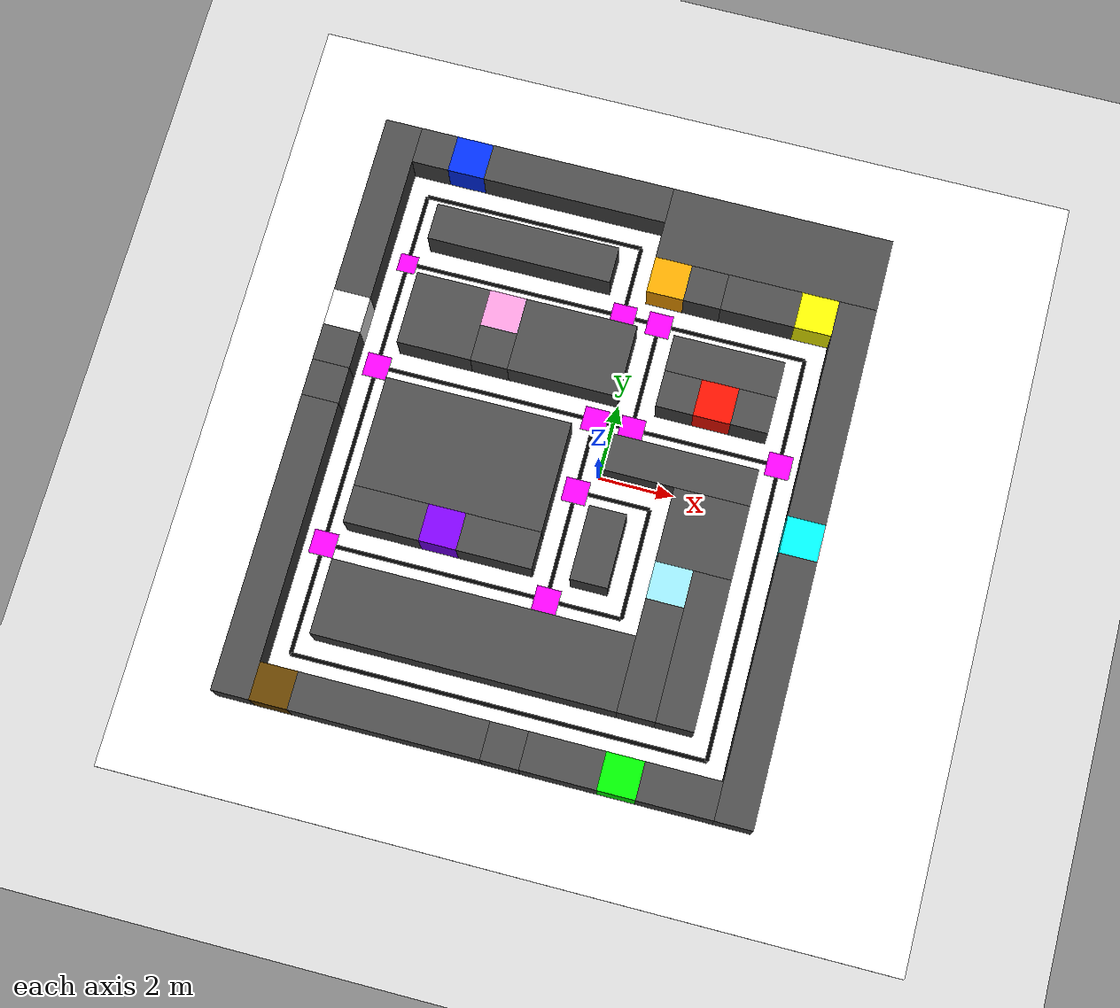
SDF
<sdf version='1.10'>
  <world name='hello_world'>
    <physics name='1ms' type='ignored'>
      <max_step_size>0.001</max_step_size>
      <real_time_factor>1</real_time_factor>
      <real_time_update_rate>1000</real_time_update_rate>
    </physics>
    <plugin name='gz::sim::systems::Physics' filename='gz-sim-physics-system'/>
    <plugin name='gz::sim::systems::UserCommands' filename='gz-sim-user-commands-system'/>
    <plugin name='gz::sim::systems::SceneBroadcaster' filename='gz-sim-scene-broadcaster-system'/>
    <plugin name='gz::sim::systems::Contact' filename='gz-sim-contact-system'/>
    <plugin name='gz::sim::systems::Sensors' filename='gz-sim-sensors-system'>
      <render_engine>ogre2</render_engine>
    </plugin>
    <gravity>0 0 -9.8000000000000007</gravity>
    <magnetic_field>5.5644999999999998e-06 2.2875799999999999e-05 -4.2388400000000002e-05</magnetic_field>
    <atmosphere type='adiabatic'/>
    <scene>
      <ambient>0.400000006 0.400000006 0.400000006 1</ambient>
      <background>0.827000022 0.80400002 1 1</background>
      <shadows>true</shadows>
    </scene>
    <model name='ground_plane'>
      <static>true</static>
      <link name='link'>
        <collision name='collision'>
          <geometry>
            <plane>
              <normal>0 0 1</normal>
              <size>100 100</size>
            </plane>
          </geometry>
          <surface>
            <friction>
              <ode/>
            </friction>
            <bounce/>
            <contact/>
          </surface>
        </collision>
        <visual name='visual'>
          <geometry>
            <plane>
              <normal>0 0 1</normal>
              <size>100 100</size>
            </plane>
          </geometry>
          <material>
            <ambient>0.800000012 0.800000012 0.800000012 1</ambient>
            <diffuse>0.800000012 0.800000012 0.800000012 1</diffuse>
            <specular>0.800000012 0.800000012 0.800000012 1</specular>
          </material>
        </visual>
        <pose>0 0 0 0 0 0</pose>
        <inertial>
          <pose>0 0 0 0 0 0</pose>
          <mass>1</mass>
          <inertia>
            <ixx>1</ixx>
            <ixy>0</ixy>
            <ixz>0</ixz>
            <iyy>1</iyy>
            <iyz>0</iyz>
            <izz>1</izz>
          </inertia>
        </inertial>
        <enable_wind>false</enable_wind>
      </link>
      <pose>0 0 0 0 0 0</pose>
      <self_collide>false</self_collide>
    </model>
    <model name='box'>
      <pose>-7.5 5.5 0.5 0 0 0</pose>
      <link name='box_link'>
        <inertial>
          <inertia>
            <ixx>0.16666</ixx>
            <ixy>0</ixy>
            <ixz>0</ixz>
            <iyy>0.16666</iyy>
            <iyz>0</iyz>
            <izz>0.16666</izz>
          </inertia>
          <mass>1</mass>
          <pose>0 0 0 0 0 0</pose>
        </inertial>
        <collision name='box_collision'>
          <geometry>
            <box>
              <size>1 5 1</size>
            </box>
          </geometry>
          <surface>
            <friction>
              <ode/>
            </friction>
            <bounce/>
            <contact/>
          </surface>
        </collision>
        <visual name='box_visual'>
          <geometry>
            <box>
              <size>1 5 1</size>
            </box>
          </geometry>
          <material>
            <ambient>0.300000012 0.300000012 0.300000012 1</ambient>
            <diffuse>0.277999997 0.277999997 0.277999997 1</diffuse>
            <specular>1 1 1 1</specular>
          </material>
        </visual>
        <pose>0 0 0 0 0 0</pose>
        <enable_wind>false</enable_wind>
      </link>
      <static>true</static>
      <self_collide>false</self_collide>
    </model>
    <model name='PO'>
      <pose>-7.5 2.5 0.5 0 0 0</pose>
      <link name='box_link'>
        <inertial>
          <inertia>
            <ixx>0.16666</ixx>
            <ixy>0</ixy>
            <ixz>0</ixz>
            <iyy>0.16666</iyy>
            <iyz>0</iyz>
            <izz>0.16666</izz>
          </inertia>
          <mass>1</mass>
          <pose>0 0 0 0 0 0</pose>
        </inertial>
        <collision name='box_collision'>
          <geometry>
            <box>
              <size>1 1 1</size>
            </box>
          </geometry>
          <surface>
            <friction>
              <ode/>
            </friction>
            <bounce/>
            <contact/>
          </surface>
        </collision>
        <visual name='box_visual'>
          <geometry>
            <box>
              <size>1 1 1</size>
            </box>
          </geometry>
          <material>
            <ambient>0.300000012 0.300000012 0.300000012 1</ambient>
            <diffuse>1 1 1 1</diffuse>
            <specular>1 1 1 1</specular>
          </material>
        </visual>
        <pose>0 0 0 0 0 0</pose>
        <enable_wind>false</enable_wind>
      </link>
      <static>true</static>
      <self_collide>false</self_collide>
    </model>
    <model name='CHARGER_0'>
      <pose>-7.5 0.5 0.5 4.6034300000052197e-07 4.603870000005235e-07 6.6837400000076367e-10</pose>
      <link name='box_link'>
        <inertial>
          <inertia>
            <ixx>0.16666</ixx>
            <ixy>0</ixy>
            <ixz>0</ixz>
            <iyy>0.16666</iyy>
            <iyz>0</iyz>
            <izz>0.16666</izz>
          </inertia>
          <mass>1</mass>
          <pose>0 0 0 0 0 0</pose>
        </inertial>
        <collision name='box_collision'>
          <geometry>
            <box>
              <size>1 1 1</size>
            </box>
          </geometry>
          <surface>
            <friction>
              <ode/>
            </friction>
            <bounce/>
            <contact/>
          </surface>
        </collision>
        <visual name='box_visual'>
          <geometry>
            <box>
              <size>1 1 1</size>
            </box>
          </geometry>
          <material>
            <ambient>0.300000012 0.300000012 0.300000012 1</ambient>
            <diffuse>0.277999997 0.277999997 0.277999997 1</diffuse>
            <specular>1 1 1 1</specular>
          </material>
        </visual>
        <pose>0 0 0 0 0 0</pose>
        <enable_wind>false</enable_wind>
      </link>
      <static>true</static>
      <self_collide>false</self_collide>
    </model>
    <model name='box_2'>
      <pose>-7.5 -4 0.5 4.6034300000052197e-07 4.603870000005235e-07 6.6837400000076367e-10</pose>
      <link name='box_link'>
        <inertial>
          <inertia>
            <ixx>0.16666</ixx>
            <ixy>0</ixy>
            <ixz>0</ixz>
            <iyy>0.16666</iyy>
            <iyz>0</iyz>
            <izz>0.16666</izz>
          </inertia>
          <mass>1</mass>
          <pose>0 0 0 0 0 0</pose>
        </inertial>
        <collision name='box_collision'>
          <geometry>
            <box>
              <size>1 8 1</size>
            </box>
          </geometry>
          <surface>
            <friction>
              <ode/>
            </friction>
            <bounce/>
            <contact/>
          </surface>
        </collision>
        <visual name='box_visual'>
          <geometry>
            <box>
              <size>1 8 1</size>
            </box>
          </geometry>
          <material>
            <ambient>0.300000012 0.300000012 0.300000012 1</ambient>
            <diffuse>0.277999997 0.277999997 0.277999997 1</diffuse>
            <specular>1 1 1 1</specular>
          </material>
        </visual>
        <pose>0 0 0 0 0 0</pose>
        <enable_wind>false</enable_wind>
      </link>
      <static>true</static>
      <self_collide>false</self_collide>
    </model>
    <model name='box_3'>
      <pose>-6.5 7.5 0.5 4.6034300000052197e-07 4.603870000005235e-07 6.6837400000076367e-10</pose>
      <link name='box_link'>
        <inertial>
          <inertia>
            <ixx>0.16666</ixx>
            <ixy>0</ixy>
            <ixz>0</ixz>
            <iyy>0.16666</iyy>
            <iyz>0</iyz>
            <izz>0.16666</izz>
          </inertia>
          <mass>1</mass>
          <pose>0 0 0 0 0 0</pose>
        </inertial>
        <collision name='box_collision'>
          <geometry>
            <box>
              <size>1 1 1</size>
            </box>
          </geometry>
          <surface>
            <friction>
              <ode/>
            </friction>
            <bounce/>
            <contact/>
          </surface>
        </collision>
        <visual name='box_visual'>
          <geometry>
            <box>
              <size>1 1 1</size>
            </box>
          </geometry>
          <material>
            <ambient>0.300000012 0.300000012 0.300000012 1</ambient>
            <diffuse>0.277999997 0.277999997 0.277999997 1</diffuse>
            <specular>1 1 1 1</specular>
          </material>
        </visual>
        <pose>0 0 0 0 0 0</pose>
        <enable_wind>false</enable_wind>
      </link>
      <static>true</static>
      <self_collide>false</self_collide>
    </model>
    <model name='HOUSE_1'>
      <pose>-5.5 7.5 0.5 4.6034300000052197e-07 4.603870000005235e-07 6.6837400000076367e-10</pose>
      <link name='box_link'>
        <inertial>
          <inertia>
            <ixx>0.16666</ixx>
            <ixy>0</ixy>
            <ixz>0</ixz>
            <iyy>0.16666</iyy>
            <iyz>0</iyz>
            <izz>0.16666</izz>
          </inertia>
          <mass>1</mass>
          <pose>0 0 0 0 0 0</pose>
        </inertial>
        <collision name='box_collision'>
          <geometry>
            <box>
              <size>1 1 1</size>
            </box>
          </geometry>
          <surface>
            <friction>
              <ode/>
            </friction>
            <bounce/>
            <contact/>
          </surface>
        </collision>
        <visual name='box_visual'>
          <geometry>
            <box>
              <size>1 1 1</size>
            </box>
          </geometry>
          <material>
            <ambient>0.300000012 0.300000012 0.300000012 1</ambient>
            <diffuse>0 0.172999993 1 1</diffuse>
            <specular>1 1 1 1</specular>
          </material>
        </visual>
        <pose>0 0 0 0 0 0</pose>
        <enable_wind>false</enable_wind>
      </link>
      <static>true</static>
      <self_collide>false</self_collide>
    </model>
    <model name='box_5'>
      <pose>-2.5 7.5 0.5 4.6034300000052197e-07 4.603870000005235e-07 6.6837400000076367e-10</pose>
      <link name='box_link'>
        <inertial>
          <inertia>
            <ixx>0.16666</ixx>
            <ixy>0</ixy>
            <ixz>0</ixz>
            <iyy>0.16666</iyy>
            <iyz>0</iyz>
            <izz>0.16666</izz>
          </inertia>
          <mass>1</mass>
          <pose>0 0 0 0 0 0</pose>
        </inertial>
        <collision name='box_collision'>
          <geometry>
            <box>
              <size>5 1 1</size>
            </box>
          </geometry>
          <surface>
            <friction>
              <ode/>
            </friction>
            <bounce/>
            <contact/>
          </surface>
        </collision>
        <visual name='box_visual'>
          <geometry>
            <box>
              <size>5 1 1</size>
            </box>
          </geometry>
          <material>
            <ambient>0.300000012 0.300000012 0.300000012 1</ambient>
            <diffuse>0.277999997 0.277999997 0.277999997 1</diffuse>
            <specular>1 1 1 1</specular>
          </material>
        </visual>
        <pose>0 0 0 0 0 0</pose>
        <enable_wind>false</enable_wind>
      </link>
      <static>true</static>
      <self_collide>false</self_collide>
    </model>
    <model name='box_6'>
      <pose>3 7 0.5 0 0 0</pose>
      <link name='box_link'>
        <inertial>
          <inertia>
            <ixx>0.16666</ixx>
            <ixy>0</ixy>
            <ixz>0</ixz>
            <iyy>0.16666</iyy>
            <iyz>0</iyz>
            <izz>0.16666</izz>
          </inertia>
          <mass>1</mass>
          <pose>0 0 0 0 0 0</pose>
        </inertial>
        <collision name='box_collision'>
          <geometry>
            <box>
              <size>6 2 1</size>
            </box>
          </geometry>
          <surface>
            <friction>
              <ode/>
            </friction>
            <bounce/>
            <contact/>
          </surface>
        </collision>
        <visual name='box_visual'>
          <geometry>
            <box>
              <size>6 2 1</size>
            </box>
          </geometry>
          <material>
            <ambient>0.300000012 0.300000012 0.300000012 1</ambient>
            <diffuse>0.277999997 0.277999997 0.277999997 1</diffuse>
            <specular>1 1 1 1</specular>
          </material>
        </visual>
        <pose>0 0 0 0 0 0</pose>
        <enable_wind>false</enable_wind>
      </link>
      <static>true</static>
      <self_collide>false</self_collide>
    </model>
    <model name='box_7'>
      <pose>5.5 3 0.5 1.6937494726750003e-43 0 0</pose>
      <link name='box_link'>
        <inertial>
          <inertia>
            <ixx>0.16666</ixx>
            <ixy>0</ixy>
            <ixz>0</ixz>
            <iyy>0.16666</iyy>
            <iyz>0</iyz>
            <izz>0.16666</izz>
          </inertia>
          <mass>1</mass>
          <pose>0 0 0 0 0 0</pose>
        </inertial>
        <collision name='box_collision'>
          <geometry>
            <box>
              <size>1 6 1</size>
            </box>
          </geometry>
          <surface>
            <friction>
              <ode/>
            </friction>
            <bounce/>
            <contact/>
          </surface>
        </collision>
        <visual name='box_visual'>
          <geometry>
            <box>
              <size>1 6 1</size>
            </box>
          </geometry>
          <material>
            <ambient>0.300000012 0.300000012 0.300000012 1</ambient>
            <diffuse>0.277999997 0.277999997 0.277999997 1</diffuse>
            <specular>1 1 1 1</specular>
          </material>
        </visual>
        <pose>0 0 0 0 0 0</pose>
        <enable_wind>false</enable_wind>
      </link>
      <static>true</static>
      <self_collide>false</self_collide>
    </model>
    <model name='HOUSE_6'>
      <pose>5.5 -0.5 0.5 4.6840416479999999e-44 0 0</pose>
      <link name='box_link'>
        <inertial>
          <inertia>
            <ixx>0.16666</ixx>
            <ixy>0</ixy>
            <ixz>0</ixz>
            <iyy>0.16666</iyy>
            <iyz>0</iyz>
            <izz>0.16666</izz>
          </inertia>
          <mass>1</mass>
          <pose>0 0 0 0 0 0</pose>
        </inertial>
        <collision name='box_collision'>
          <geometry>
            <box>
              <size>1 1 1</size>
            </box>
          </geometry>
          <surface>
            <friction>
              <ode/>
            </friction>
            <bounce/>
            <contact/>
          </surface>
        </collision>
        <visual name='box_visual'>
          <geometry>
            <box>
              <size>1 1 1</size>
            </box>
          </geometry>
          <material>
            <ambient>0.300000012 0.300000012 0.300000012 1</ambient>
            <diffuse>0 0.984000027 1 1</diffuse>
            <specular>1 1 1 1</specular>
          </material>
        </visual>
        <pose>0 0 0 0 0 0</pose>
        <enable_wind>false</enable_wind>
      </link>
      <static>true</static>
      <self_collide>false</self_collide>
    </model>
    <model name='box_9'>
      <pose>5.5 -4.5 0.5 -8.9888212590000021e-45 0 0</pose>
      <link name='box_link'>
        <inertial>
          <inertia>
            <ixx>0.16666</ixx>
            <ixy>0</ixy>
            <ixz>0</ixz>
            <iyy>0.16666</iyy>
            <iyz>0</iyz>
            <izz>0.16666</izz>
          </inertia>
          <mass>1</mass>
          <pose>0 0 0 0 0 0</pose>
        </inertial>
        <collision name='box_collision'>
          <geometry>
            <box>
              <size>1 7 1</size>
            </box>
          </geometry>
          <surface>
            <friction>
              <ode/>
            </friction>
            <bounce/>
            <contact/>
          </surface>
        </collision>
        <visual name='box_visual'>
          <geometry>
            <box>
              <size>1 7 1</size>
            </box>
          </geometry>
          <material>
            <ambient>0.300000012 0.300000012 0.300000012 1</ambient>
            <diffuse>0.277999997 0.277999997 0.277999997 1</diffuse>
            <specular>1 1 1 1</specular>
          </material>
        </visual>
        <pose>0 0 0 0 0 0</pose>
        <enable_wind>false</enable_wind>
      </link>
      <static>true</static>
      <self_collide>false</self_collide>
    </model>
    <model name='box_10'>
      <pose>4 -7.5 0.5 0 0 0</pose>
      <link name='box_link'>
        <inertial>
          <inertia>
            <ixx>0.16666</ixx>
            <ixy>0</ixy>
            <ixz>0</ixz>
            <iyy>0.16666</iyy>
            <iyz>0</iyz>
            <izz>0.16666</izz>
          </inertia>
          <mass>1</mass>
          <pose>0 0 0 0 0 0</pose>
        </inertial>
        <collision name='box_collision'>
          <geometry>
            <box>
              <size>2 1 1</size>
            </box>
          </geometry>
          <surface>
            <friction>
              <ode/>
            </friction>
            <bounce/>
            <contact/>
          </surface>
        </collision>
        <visual name='box_visual'>
          <geometry>
            <box>
              <size>2 1 1</size>
            </box>
          </geometry>
          <material>
            <ambient>0.300000012 0.300000012 0.300000012 1</ambient>
            <diffuse>0.277999997 0.277999997 0.277999997 1</diffuse>
            <specular>1 1 1 1</specular>
          </material>
        </visual>
        <pose>0 0 0 0 0 0</pose>
        <enable_wind>false</enable_wind>
      </link>
      <static>true</static>
      <self_collide>false</self_collide>
    </model>
    <model name='HOUSE_9'>
      <pose>2.5 -7.5 0.5 0 0 0</pose>
      <link name='box_link'>
        <inertial>
          <inertia>
            <ixx>0.16666</ixx>
            <ixy>0</ixy>
            <ixz>0</ixz>
            <iyy>0.16666</iyy>
            <iyz>0</iyz>
            <izz>0.16666</izz>
          </inertia>
          <mass>1</mass>
          <pose>0 0 0 0 0 0</pose>
        </inertial>
        <collision name='box_collision'>
          <geometry>
            <box>
              <size>1 1 1</size>
            </box>
          </geometry>
          <surface>
            <friction>
              <ode/>
            </friction>
            <bounce/>
            <contact/>
          </surface>
        </collision>
        <visual name='box_visual'>
          <geometry>
            <box>
              <size>1 1 1</size>
            </box>
          </geometry>
          <material>
            <ambient>0.300000012 0.300000012 0.300000012 1</ambient>
            <diffuse>0 1 0 1</diffuse>
            <specular>1 1 1 1</specular>
          </material>
        </visual>
        <pose>0 0 0 0 0 0</pose>
        <enable_wind>false</enable_wind>
      </link>
      <static>true</static>
      <self_collide>false</self_collide>
    </model>
    <model name='box_12'>
      <pose>1 -7.5 0.5 0 0 0</pose>
      <link name='box_link'>
        <inertial>
          <inertia>
            <ixx>0.16666</ixx>
            <ixy>0</ixy>
            <ixz>0</ixz>
            <iyy>0.16666</iyy>
            <iyz>0</iyz>
            <izz>0.16666</izz>
          </inertia>
          <mass>1</mass>
          <pose>0 0 0 0 0 0</pose>
        </inertial>
        <collision name='box_collision'>
          <geometry>
            <box>
              <size>2 1 1</size>
            </box>
          </geometry>
          <surface>
            <friction>
              <ode/>
            </friction>
            <bounce/>
            <contact/>
          </surface>
        </collision>
        <visual name='box_visual'>
          <geometry>
            <box>
              <size>2 1 1</size>
            </box>
          </geometry>
          <material>
            <ambient>0.300000012 0.300000012 0.300000012 1</ambient>
            <diffuse>0.277999997 0.277999997 0.277999997 1</diffuse>
            <specular>1 1 1 1</specular>
          </material>
        </visual>
        <pose>0 0 0 0 0 0</pose>
        <enable_wind>false</enable_wind>
      </link>
      <static>true</static>
      <self_collide>false</self_collide>
    </model>
    <model name='CHARGER_2'>
      <pose>-0.5 -7.5 0.5 0 0 0</pose>
      <link name='box_link'>
        <inertial>
          <inertia>
            <ixx>0.16666</ixx>
            <ixy>0</ixy>
            <ixz>0</ixz>
            <iyy>0.16666</iyy>
            <iyz>0</iyz>
            <izz>0.16666</izz>
          </inertia>
          <mass>1</mass>
          <pose>0 0 0 0 0 0</pose>
        </inertial>
        <collision name='box_collision'>
          <geometry>
            <box>
              <size>1 1 1</size>
            </box>
          </geometry>
          <surface>
            <friction>
              <ode/>
            </friction>
            <bounce/>
            <contact/>
          </surface>
        </collision>
        <visual name='box_visual'>
          <geometry>
            <box>
              <size>1 1 1</size>
            </box>
          </geometry>
          <material>
            <ambient>0.300000012 0.300000012 0.300000012 1</ambient>
            <diffuse>0.277999997 0.277999997 0.277999997 1</diffuse>
            <specular>1 1 1 1</specular>
          </material>
        </visual>
        <pose>0 0 0 0 0 0</pose>
        <enable_wind>false</enable_wind>
      </link>
      <static>true</static>
      <self_collide>false</self_collide>
    </model>
    <model name='box_14'>
      <pose>-3.5 -7.5 0.5 0 0 0</pose>
      <link name='box_link'>
        <inertial>
          <inertia>
            <ixx>0.16666</ixx>
            <ixy>0</ixy>
            <ixz>0</ixz>
            <iyy>0.16666</iyy>
            <iyz>0</iyz>
            <izz>0.16666</izz>
          </inertia>
          <mass>1</mass>
          <pose>0 0 0 0 0 0</pose>
        </inertial>
        <collision name='box_collision'>
          <geometry>
            <box>
              <size>5 1 1</size>
            </box>
          </geometry>
          <surface>
            <friction>
              <ode/>
            </friction>
            <bounce/>
            <contact/>
          </surface>
        </collision>
        <visual name='box_visual'>
          <geometry>
            <box>
              <size>5 1 1</size>
            </box>
          </geometry>
          <material>
            <ambient>0.300000012 0.300000012 0.300000012 1</ambient>
            <diffuse>0.277999997 0.277999997 0.277999997 1</diffuse>
            <specular>1 1 1 1</specular>
          </material>
        </visual>
        <pose>0 0 0 0 0 0</pose>
        <enable_wind>false</enable_wind>
      </link>
      <static>true</static>
      <self_collide>false</self_collide>
    </model>
    <model name='HOUSE_7'>
      <pose>-6.5 -7.5 0.5 0 0 0</pose>
      <link name='box_link'>
        <inertial>
          <inertia>
            <ixx>0.16666</ixx>
            <ixy>0</ixy>
            <ixz>0</ixz>
            <iyy>0.16666</iyy>
            <iyz>0</iyz>
            <izz>0.16666</izz>
          </inertia>
          <mass>1</mass>
          <pose>0 0 0 0 0 0</pose>
        </inertial>
        <collision name='box_collision'>
          <geometry>
            <box>
              <size>1 1 1</size>
            </box>
          </geometry>
          <surface>
            <friction>
              <ode/>
            </friction>
            <bounce/>
            <contact/>
          </surface>
        </collision>
        <visual name='box_visual'>
          <geometry>
            <box>
              <size>1 1 1</size>
            </box>
          </geometry>
          <material>
            <ambient>0.300000012 0.300000012 0.300000012 1</ambient>
            <diffuse>0.379999995 0.246999994 0 1</diffuse>
            <specular>1 1 1 1</specular>
          </material>
        </visual>
        <pose>0 0 0 0 0 0</pose>
        <enable_wind>false</enable_wind>
      </link>
      <static>true</static>
      <self_collide>false</self_collide>
    </model>
    <model name='box_16'>
      <pose>-3.5 5.5000000000000004 0.5 0 0 0</pose>
      <link name='box_link'>
        <inertial>
          <inertia>
            <ixx>0.16666</ixx>
            <ixy>0</ixy>
            <ixz>0</ixz>
            <iyy>0.16666</iyy>
            <iyz>0</iyz>
            <izz>0.16666</izz>
          </inertia>
          <mass>1</mass>
          <pose>0 0 0 0 0 0</pose>
        </inertial>
        <collision name='box_collision'>
          <geometry>
            <box>
              <size>5 1 1</size>
            </box>
          </geometry>
          <surface>
            <friction>
              <ode/>
            </friction>
            <bounce/>
            <contact/>
          </surface>
        </collision>
        <visual name='box_visual'>
          <geometry>
            <box>
              <size>5 1 1</size>
            </box>
          </geometry>
          <material>
            <ambient>0.300000012 0.300000012 0.300000012 1</ambient>
            <diffuse>0.277999997 0.277999997 0.277999997 1</diffuse>
            <specular>1 1 1 1</specular>
          </material>
        </visual>
        <pose>0 0 0 0 0 0</pose>
        <enable_wind>false</enable_wind>
      </link>
      <static>true</static>
      <self_collide>false</self_collide>
    </model>
    <model name='HOUSE_3'>
      <pose>0.5 5.5 0.5 0 0 0</pose>
      <link name='box_link'>
        <inertial>
          <inertia>
            <ixx>0.16666</ixx>
            <ixy>0</ixy>
            <ixz>0</ixz>
            <iyy>0.16666</iyy>
            <iyz>0</iyz>
            <izz>0.16666</izz>
          </inertia>
          <mass>1</mass>
          <pose>0 0 0 0 0 0</pose>
        </inertial>
        <collision name='box_collision'>
          <geometry>
            <box>
              <size>1 1 1</size>
            </box>
          </geometry>
          <surface>
            <friction>
              <ode/>
            </friction>
            <bounce/>
            <contact/>
          </surface>
        </collision>
        <visual name='box_visual'>
          <geometry>
            <box>
              <size>1 1 1</size>
            </box>
          </geometry>
          <material>
            <ambient>1 0.647000015 0 1</ambient>
            <diffuse>1 0.630999982 0 1</diffuse>
            <specular>1 1 1 1</specular>
          </material>
        </visual>
        <pose>0 0 0 0 0 0</pose>
        <enable_wind>false</enable_wind>
      </link>
      <static>true</static>
      <self_collide>false</self_collide>
    </model>
    <model name='CHARGER_1'>
      <pose>1.5 5.5 0.5 0 0 0</pose>
      <link name='box_link'>
        <inertial>
          <inertia>
            <ixx>0.16666</ixx>
            <ixy>0</ixy>
            <ixz>0</ixz>
            <iyy>0.16666</iyy>
            <iyz>0</iyz>
            <izz>0.16666</izz>
          </inertia>
          <mass>1</mass>
          <pose>0 0 0 0 0 0</pose>
        </inertial>
        <collision name='box_collision'>
          <geometry>
            <box>
              <size>1 1 1</size>
            </box>
          </geometry>
          <surface>
            <friction>
              <ode/>
            </friction>
            <bounce/>
            <contact/>
          </surface>
        </collision>
        <visual name='box_visual'>
          <geometry>
            <box>
              <size>1 1 1</size>
            </box>
          </geometry>
          <material>
            <ambient>0.300000012 0.300000012 0.300000012 1</ambient>
            <diffuse>0.277999997 0.277999997 0.277999997 1</diffuse>
            <specular>1 1 1 1</specular>
          </material>
        </visual>
        <pose>0 0 0 0 0 0</pose>
        <enable_wind>false</enable_wind>
      </link>
      <static>true</static>
      <self_collide>false</self_collide>
    </model>
    <model name='box_19'>
      <pose>3 5.5 0.5 0 0 0</pose>
      <link name='box_link'>
        <inertial>
          <inertia>
            <ixx>0.16666</ixx>
            <ixy>0</ixy>
            <ixz>0</ixz>
            <iyy>0.16666</iyy>
            <iyz>0</iyz>
            <izz>0.16666</izz>
          </inertia>
          <mass>1</mass>
          <pose>0 0 0 0 0 0</pose>
        </inertial>
        <collision name='box_collision'>
          <geometry>
            <box>
              <size>2 1 1</size>
            </box>
          </geometry>
          <surface>
            <friction>
              <ode/>
            </friction>
            <bounce/>
            <contact/>
          </surface>
        </collision>
        <visual name='box_visual'>
          <geometry>
            <box>
              <size>2 1 1</size>
            </box>
          </geometry>
          <material>
            <ambient>0.300000012 0.300000012 0.300000012 1</ambient>
            <diffuse>0.277999997 0.277999997 0.277999997 1</diffuse>
            <specular>1 1 1 1</specular>
          </material>
        </visual>
        <pose>0 0 0 0 0 0</pose>
        <enable_wind>false</enable_wind>
      </link>
      <static>true</static>
      <self_collide>false</self_collide>
    </model>
    <model name='HOUSE_2'>
      <pose>4.5 5.5 0.5 0 0 0</pose>
      <link name='box_link'>
        <inertial>
          <inertia>
            <ixx>0.16666</ixx>
            <ixy>0</ixy>
            <ixz>0</ixz>
            <iyy>0.16666</iyy>
            <iyz>0</iyz>
            <izz>0.16666</izz>
          </inertia>
          <mass>1</mass>
          <pose>0 0 0 0 0 0</pose>
        </inertial>
        <collision name='box_collision'>
          <geometry>
            <box>
              <size>1 1 1</size>
            </box>
          </geometry>
          <surface>
            <friction>
              <ode/>
            </friction>
            <bounce/>
            <contact/>
          </surface>
        </collision>
        <visual name='box_visual'>
          <geometry>
            <box>
              <size>1 1 1</size>
            </box>
          </geometry>
          <material>
            <ambient>0.300000012 0.300000012 0.300000012 1</ambient>
            <diffuse>0.991999984 1 0 1</diffuse>
            <specular>1 1 1 1</specular>
          </material>
        </visual>
        <pose>0 0 0 0 0 0</pose>
        <enable_wind>false</enable_wind>
      </link>
      <static>true</static>
      <self_collide>false</self_collide>
    </model>
    <model name='box_21'>
      <pose>2.5 3.5 0.5 0 0 0</pose>
      <link name='box_link'>
        <inertial>
          <inertia>
            <ixx>0.16666</ixx>
            <ixy>0</ixy>
            <ixz>0</ixz>
            <iyy>0.16666</iyy>
            <iyz>0</iyz>
            <izz>0.16666</izz>
          </inertia>
          <mass>1</mass>
          <pose>0 0 0 0 0 0</pose>
        </inertial>
        <collision name='box_collision'>
          <geometry>
            <box>
              <size>3 1 1</size>
            </box>
          </geometry>
          <surface>
            <friction>
              <ode/>
            </friction>
            <bounce/>
            <contact/>
          </surface>
        </collision>
        <visual name='box_visual'>
          <geometry>
            <box>
              <size>3 1 1</size>
            </box>
          </geometry>
          <material>
            <ambient>0.300000012 0.300000012 0.300000012 1</ambient>
            <diffuse>0.277999997 0.277999997 0.277999997 1</diffuse>
            <specular>1 1 1 1</specular>
          </material>
        </visual>
        <pose>0 0 0 0 0 0</pose>
        <enable_wind>false</enable_wind>
      </link>
      <static>true</static>
      <self_collide>false</self_collide>
    </model>
    <model name='box_22'>
      <pose>3.5 2.5 0.5 0 0 0</pose>
      <link name='box_link'>
        <inertial>
          <inertia>
            <ixx>0.16666</ixx>
            <ixy>0</ixy>
            <ixz>0</ixz>
            <iyy>0.16666</iyy>
            <iyz>0</iyz>
            <izz>0.16666</izz>
          </inertia>
          <mass>1</mass>
          <pose>0 0 0 0 0 0</pose>
        </inertial>
        <collision name='box_collision'>
          <geometry>
            <box>
              <size>1 1 1</size>
            </box>
          </geometry>
          <surface>
            <friction>
              <ode/>
            </friction>
            <bounce/>
            <contact/>
          </surface>
        </collision>
        <visual name='box_visual'>
          <geometry>
            <box>
              <size>1 1 1</size>
            </box>
          </geometry>
          <material>
            <ambient>0.300000012 0.300000012 0.300000012 1</ambient>
            <diffuse>0.277999997 0.277999997 0.277999997 1</diffuse>
            <specular>1 1 1 1</specular>
          </material>
        </visual>
        <pose>0 0 0 0 0 0</pose>
        <enable_wind>false</enable_wind>
      </link>
      <static>true</static>
      <self_collide>false</self_collide>
    </model>
    <model name='HOUSE_5'>
      <pose>2.5 2.5 0.5 0 0 0</pose>
      <link name='box_link'>
        <inertial>
          <inertia>
            <ixx>0.16666</ixx>
            <ixy>0</ixy>
            <ixz>0</ixz>
            <iyy>0.16666</iyy>
            <iyz>0</iyz>
            <izz>0.16666</izz>
          </inertia>
          <mass>1</mass>
          <pose>0 0 0 0 0 0</pose>
        </inertial>
        <collision name='box_collision'>
          <geometry>
            <box>
              <size>1 1 1</size>
            </box>
          </geometry>
          <surface>
            <friction>
              <ode/>
            </friction>
            <bounce/>
            <contact/>
          </surface>
        </collision>
        <visual name='box_visual'>
          <geometry>
            <box>
              <size>1 1 1</size>
            </box>
          </geometry>
          <material>
            <ambient>0.300000012 0.300000012 0.300000012 1</ambient>
            <diffuse>1 0.063000001 0 1</diffuse>
            <specular>1 1 1 1</specular>
          </material>
        </visual>
        <pose>0 0 0 0 0 0</pose>
        <enable_wind>false</enable_wind>
      </link>
      <static>true</static>
      <self_collide>false</self_collide>
    </model>
    <model name='box_24'>
      <pose>1.5 2.5 0.5 0 0 0</pose>
      <link name='box_link'>
        <inertial>
          <inertia>
            <ixx>0.16666</ixx>
            <ixy>0</ixy>
            <ixz>0</ixz>
            <iyy>0.16666</iyy>
            <iyz>0</iyz>
            <izz>0.16666</izz>
          </inertia>
          <mass>1</mass>
          <pose>0 0 0 0 0 0</pose>
        </inertial>
        <collision name='box_collision'>
          <geometry>
            <box>
              <size>1 1 1</size>
            </box>
          </geometry>
          <surface>
            <friction>
              <ode/>
            </friction>
            <bounce/>
            <contact/>
          </surface>
        </collision>
        <visual name='box_visual'>
          <geometry>
            <box>
              <size>1 1 1</size>
            </box>
          </geometry>
          <material>
            <ambient>0.300000012 0.300000012 0.300000012 1</ambient>
            <diffuse>0.277999997 0.277999997 0.277999997 1</diffuse>
            <specular>1 1 1 1</specular>
          </material>
        </visual>
        <pose>0 0 0 0 0 0</pose>
        <enable_wind>false</enable_wind>
      </link>
      <static>true</static>
      <self_collide>false</self_collide>
    </model>
    <model name='box_25'>
      <pose>-1.5 3 0.5 0 0 0</pose>
      <link name='box_link'>
        <inertial>
          <inertia>
            <ixx>0.16666</ixx>
            <ixy>0</ixy>
            <ixz>0</ixz>
            <iyy>0.16666</iyy>
            <iyz>0</iyz>
            <izz>0.16666</izz>
          </inertia>
          <mass>1</mass>
          <pose>0 0 0 0 0 0</pose>
        </inertial>
        <collision name='box_collision'>
          <geometry>
            <box>
              <size>3 2 1</size>
            </box>
          </geometry>
          <surface>
            <friction>
              <ode/>
            </friction>
            <bounce/>
            <contact/>
          </surface>
        </collision>
        <visual name='box_visual'>
          <geometry>
            <box>
              <size>3 2 1</size>
            </box>
          </geometry>
          <material>
            <ambient>0.300000012 0.300000012 0.300000012 1</ambient>
            <diffuse>0.277999997 0.277999997 0.277999997 1</diffuse>
            <specular>1 1 1 1</specular>
          </material>
        </visual>
        <pose>0 0 0 0 0 0</pose>
        <enable_wind>false</enable_wind>
      </link>
      <static>true</static>
      <self_collide>false</self_collide>
    </model>
    <model name='HOUSE_4'>
      <pose>-3.5 3.5 0.5 0 0 0</pose>
      <link name='box_link'>
        <inertial>
          <inertia>
            <ixx>0.16666</ixx>
            <ixy>0</ixy>
            <ixz>0</ixz>
            <iyy>0.16666</iyy>
            <iyz>0</iyz>
            <izz>0.16666</izz>
          </inertia>
          <mass>1</mass>
          <pose>0 0 0 0 0 0</pose>
        </inertial>
        <collision name='box_collision'>
          <geometry>
            <box>
              <size>1 1 1</size>
            </box>
          </geometry>
          <surface>
            <friction>
              <ode/>
            </friction>
            <bounce/>
            <contact/>
          </surface>
        </collision>
        <visual name='box_visual'>
          <geometry>
            <box>
              <size>1 1 1</size>
            </box>
          </geometry>
          <material>
            <ambient>0.300000012 0.300000012 0.300000012 1</ambient>
            <diffuse>0.987999976 0.583999991 0.819999993 1</diffuse>
            <specular>1 1 1 1</specular>
          </material>
        </visual>
        <pose>0 0 0 0 0 0</pose>
        <enable_wind>false</enable_wind>
      </link>
      <static>true</static>
      <self_collide>false</self_collide>
    </model>
    <model name='box_27'>
      <pose>-3.5 2.5 0.5 0 0 0</pose>
      <link name='box_link'>
        <inertial>
          <inertia>
            <ixx>0.16666</ixx>
            <ixy>0</ixy>
            <ixz>0</ixz>
            <iyy>0.16666</iyy>
            <iyz>0</iyz>
            <izz>0.16666</izz>
          </inertia>
          <mass>1</mass>
          <pose>0 0 0 0 0 0</pose>
        </inertial>
        <collision name='box_collision'>
          <geometry>
            <box>
              <size>1 1 1</size>
            </box>
          </geometry>
          <surface>
            <friction>
              <ode/>
            </friction>
            <bounce/>
            <contact/>
          </surface>
        </collision>
        <visual name='box_visual'>
          <geometry>
            <box>
              <size>1 1 1</size>
            </box>
          </geometry>
          <material>
            <ambient>0.300000012 0.300000012 0.300000012 1</ambient>
            <diffuse>0.277999997 0.277999997 0.277999997 1</diffuse>
            <specular>1 1 1 1</specular>
          </material>
        </visual>
        <pose>0 0 0 0 0 0</pose>
        <enable_wind>false</enable_wind>
      </link>
      <static>true</static>
      <self_collide>false</self_collide>
    </model>
    <model name='box_28'>
      <pose>-5 3 0.5 0 0 0</pose>
      <link name='box_link'>
        <inertial>
          <inertia>
            <ixx>0.16666</ixx>
            <ixy>0</ixy>
            <ixz>0</ixz>
            <iyy>0.16666</iyy>
            <iyz>0</iyz>
            <izz>0.16666</izz>
          </inertia>
          <mass>1</mass>
          <pose>0 0 0 0 0 0</pose>
        </inertial>
        <collision name='box_collision'>
          <geometry>
            <box>
              <size>2 2 1</size>
            </box>
          </geometry>
          <surface>
            <friction>
              <ode/>
            </friction>
            <bounce/>
            <contact/>
          </surface>
        </collision>
        <visual name='box_visual'>
          <geometry>
            <box>
              <size>2 2 1</size>
            </box>
          </geometry>
          <material>
            <ambient>0.300000012 0.300000012 0.300000012 1</ambient>
            <diffuse>0.277999997 0.277999997 0.277999997 1</diffuse>
            <specular>1 1 1 1</specular>
          </material>
        </visual>
        <pose>0 0 0 0 0 0</pose>
        <enable_wind>false</enable_wind>
      </link>
      <static>true</static>
      <self_collide>false</self_collide>
    </model>
    <model name='box_29'>
      <pose>-3.5 -0.5 0.5 0 0 0</pose>
      <link name='box_link'>
        <inertial>
          <inertia>
            <ixx>0.16666</ixx>
            <ixy>0</ixy>
            <ixz>0</ixz>
            <iyy>0.16666</iyy>
            <iyz>0</iyz>
            <izz>0.16666</izz>
          </inertia>
          <mass>1</mass>
          <pose>0 0 0 0 0 0</pose>
        </inertial>
        <collision name='box_collision'>
          <geometry>
            <box>
              <size>5 3 1</size>
            </box>
          </geometry>
          <surface>
            <friction>
              <ode/>
            </friction>
            <bounce/>
            <contact/>
          </surface>
        </collision>
        <visual name='box_visual'>
          <geometry>
            <box>
              <size>5 3 1</size>
            </box>
          </geometry>
          <material>
            <ambient>0.300000012 0.300000012 0.300000012 1</ambient>
            <diffuse>0.277999997 0.277999997 0.277999997 1</diffuse>
            <specular>1 1 1 1</specular>
          </material>
        </visual>
        <pose>0 0 0 0 0 0</pose>
        <enable_wind>false</enable_wind>
      </link>
      <static>true</static>
      <self_collide>false</self_collide>
    </model>
    <model name='box_30'>
      <pose>-5 -2.5 0.5 0 0 0</pose>
      <link name='box_link'>
        <inertial>
          <inertia>
            <ixx>0.16666</ixx>
            <ixy>0</ixy>
            <ixz>0</ixz>
            <iyy>0.16666</iyy>
            <iyz>0</iyz>
            <izz>0.16666</izz>
          </inertia>
          <mass>1</mass>
          <pose>0 0 0 0 0 0</pose>
        </inertial>
        <collision name='box_collision'>
          <geometry>
            <box>
              <size>2 1 1</size>
            </box>
          </geometry>
          <surface>
            <friction>
              <ode/>
            </friction>
            <bounce/>
            <contact/>
          </surface>
        </collision>
        <visual name='box_visual'>
          <geometry>
            <box>
              <size>2 1 1</size>
            </box>
          </geometry>
          <material>
            <ambient>0.300000012 0.300000012 0.300000012 1</ambient>
            <diffuse>0.277999997 0.277999997 0.277999997 1</diffuse>
            <specular>1 1 1 1</specular>
          </material>
        </visual>
        <pose>0 0 0 0 0 0</pose>
        <enable_wind>false</enable_wind>
      </link>
      <static>true</static>
      <self_collide>false</self_collide>
    </model>
    <model name='HOUSE_8'>
      <pose>-3.5 -2.5 0.5 0 0 0</pose>
      <link name='box_link'>
        <inertial>
          <inertia>
            <ixx>0.16666</ixx>
            <ixy>0</ixy>
            <ixz>0</ixz>
            <iyy>0.16666</iyy>
            <iyz>0</iyz>
            <izz>0.16666</izz>
          </inertia>
          <mass>1</mass>
          <pose>0 0 0 0 0 0</pose>
        </inertial>
        <collision name='box_collision'>
          <geometry>
            <box>
              <size>1 1 1</size>
            </box>
          </geometry>
          <surface>
            <friction>
              <ode/>
            </friction>
            <bounce/>
            <contact/>
          </surface>
        </collision>
        <visual name='box_visual'>
          <geometry>
            <box>
              <size>1 1 1</size>
            </box>
          </geometry>
          <material>
            <ambient>0.300000012 0.300000012 0.300000012 1</ambient>
            <diffuse>0.470999986 0 1 1</diffuse>
            <specular>1 1 1 1</specular>
          </material>
        </visual>
        <pose>0 0 0 0 0 0</pose>
        <enable_wind>false</enable_wind>
      </link>
      <static>true</static>
      <self_collide>false</self_collide>
    </model>
    <model name='box_32'>
      <pose>-2 -2.5 0.5 0 0 0</pose>
      <link name='box_link'>
        <inertial>
          <inertia>
            <ixx>0.16666</ixx>
            <ixy>0</ixy>
            <ixz>0</ixz>
            <iyy>0.16666</iyy>
            <iyz>0</iyz>
            <izz>0.16666</izz>
          </inertia>
          <mass>1</mass>
          <pose>0 0 0 0 0 0</pose>
        </inertial>
        <collision name='box_collision'>
          <geometry>
            <box>
              <size>2 1 1</size>
            </box>
          </geometry>
          <surface>
            <friction>
              <ode/>
            </friction>
            <bounce/>
            <contact/>
          </surface>
        </collision>
        <visual name='box_visual'>
          <geometry>
            <box>
              <size>2 1 1</size>
            </box>
          </geometry>
          <material>
            <ambient>0.300000012 0.300000012 0.300000012 1</ambient>
            <diffuse>0.277999997 0.277999997 0.277999997 1</diffuse>
            <specular>1 1 1 1</specular>
          </material>
        </visual>
        <pose>0 0 0 0 0 0</pose>
        <enable_wind>false</enable_wind>
      </link>
      <static>true</static>
      <self_collide>false</self_collide>
    </model>
    <model name='box_33'>
      <pose>0.5 -2 0.5 0 0 0</pose>
      <link name='box_link'>
        <inertial>
          <inertia>
            <ixx>0.16666</ixx>
            <ixy>0</ixy>
            <ixz>0</ixz>
            <iyy>0.16666</iyy>
            <iyz>0</iyz>
            <izz>0.16666</izz>
          </inertia>
          <mass>1</mass>
          <pose>0 0 0 0 0 0</pose>
        </inertial>
        <collision name='box_collision'>
          <geometry>
            <box>
              <size>1 2 1</size>
            </box>
          </geometry>
          <surface>
            <friction>
              <ode/>
            </friction>
            <bounce/>
            <contact/>
          </surface>
        </collision>
        <visual name='box_visual'>
          <geometry>
            <box>
              <size>1 2 1</size>
            </box>
          </geometry>
          <material>
            <ambient>0.300000012 0.300000012 0.300000012 1</ambient>
            <diffuse>0.277999997 0.277999997 0.277999997 1</diffuse>
            <specular>1 1 1 1</specular>
          </material>
        </visual>
        <pose>0 0 0 0 0 0</pose>
        <enable_wind>false</enable_wind>
      </link>
      <static>true</static>
      <self_collide>false</self_collide>
    </model>
    <model name='box_34'>
      <pose>2 0.5 0.5 0 0 0</pose>
      <link name='box_link'>
        <inertial>
          <inertia>
            <ixx>0.16666</ixx>
            <ixy>0</ixy>
            <ixz>0</ixz>
            <iyy>0.16666</iyy>
            <iyz>0</iyz>
            <izz>0.16666</izz>
          </inertia>
          <mass>1</mass>
          <pose>0 0 0 0 0 0</pose>
        </inertial>
        <collision name='box_collision'>
          <geometry>
            <box>
              <size>4 1 1</size>
            </box>
          </geometry>
          <surface>
            <friction>
              <ode/>
            </friction>
            <bounce/>
            <contact/>
          </surface>
        </collision>
        <visual name='box_visual'>
          <geometry>
            <box>
              <size>4 1 1</size>
            </box>
          </geometry>
          <material>
            <ambient>0.300000012 0.300000012 0.300000012 1</ambient>
            <diffuse>0.277999997 0.277999997 0.277999997 1</diffuse>
            <specular>1 1 1 1</specular>
          </material>
        </visual>
        <pose>0 0 0 0 0 0</pose>
        <enable_wind>false</enable_wind>
      </link>
      <static>true</static>
      <self_collide>false</self_collide>
    </model>
    <model name='box_35'>
      <pose>3 -1 0.5 0 0 0</pose>
      <link name='box_link'>
        <inertial>
          <inertia>
            <ixx>0.16666</ixx>
            <ixy>0</ixy>
            <ixz>0</ixz>
            <iyy>0.16666</iyy>
            <iyz>0</iyz>
            <izz>0.16666</izz>
          </inertia>
          <mass>1</mass>
          <pose>0 0 0 0 0 0</pose>
        </inertial>
        <collision name='box_collision'>
          <geometry>
            <box>
              <size>2 2 1</size>
            </box>
          </geometry>
          <surface>
            <friction>
              <ode/>
            </friction>
            <bounce/>
            <contact/>
          </surface>
        </collision>
        <visual name='box_visual'>
          <geometry>
            <box>
              <size>2 2 1</size>
            </box>
          </geometry>
          <material>
            <ambient>0.300000012 0.300000012 0.300000012 1</ambient>
            <diffuse>0.277999997 0.277999997 0.277999997 1</diffuse>
            <specular>1 1 1 1</specular>
          </material>
        </visual>
        <pose>0 0 0 0 0 0</pose>
        <enable_wind>false</enable_wind>
      </link>
      <static>true</static>
      <self_collide>false</self_collide>
    </model>
    <model name='box_36'>
      <pose>3.5 -4 0.5 0 0 0</pose>
      <link name='box_link'>
        <inertial>
          <inertia>
            <ixx>0.16666</ixx>
            <ixy>0</ixy>
            <ixz>0</ixz>
            <iyy>0.16666</iyy>
            <iyz>0</iyz>
            <izz>0.16666</izz>
          </inertia>
          <mass>1</mass>
          <pose>0 0 0 0 0 0</pose>
        </inertial>
        <collision name='box_collision'>
          <geometry>
            <box>
              <size>1 4 1</size>
            </box>
          </geometry>
          <surface>
            <friction>
              <ode/>
            </friction>
            <bounce/>
            <contact/>
          </surface>
        </collision>
        <visual name='box_visual'>
          <geometry>
            <box>
              <size>1 4 1</size>
            </box>
          </geometry>
          <material>
            <ambient>0.300000012 0.300000012 0.300000012 1</ambient>
            <diffuse>0.277999997 0.277999997 0.277999997 1</diffuse>
            <specular>1 1 1 1</specular>
          </material>
        </visual>
        <pose>0 0 0 0 0 0</pose>
        <enable_wind>false</enable_wind>
      </link>
      <static>true</static>
      <self_collide>false</self_collide>
    </model>
    <model name='box_37'>
      <pose>2.5 -4.5 0.5 0 0 0</pose>
      <link name='box_link'>
        <inertial>
          <inertia>
            <ixx>0.16666</ixx>
            <ixy>0</ixy>
            <ixz>0</ixz>
            <iyy>0.16666</iyy>
            <iyz>0</iyz>
            <izz>0.16666</izz>
          </inertia>
          <mass>1</mass>
          <pose>0 0 0 0 0 0</pose>
        </inertial>
        <collision name='box_collision'>
          <geometry>
            <box>
              <size>1 3 1</size>
            </box>
          </geometry>
          <surface>
            <friction>
              <ode/>
            </friction>
            <bounce/>
            <contact/>
          </surface>
        </collision>
        <visual name='box_visual'>
          <geometry>
            <box>
              <size>1 3 1</size>
            </box>
          </geometry>
          <material>
            <ambient>0.300000012 0.300000012 0.300000012 1</ambient>
            <diffuse>0.277999997 0.277999997 0.277999997 1</diffuse>
            <specular>1 1 1 1</specular>
          </material>
        </visual>
        <pose>0 0 0 0 0 0</pose>
        <enable_wind>false</enable_wind>
      </link>
      <static>true</static>
      <self_collide>false</self_collide>
    </model>
    <model name='box_38'>
      <pose>-2 -5 0.5 0 0 0</pose>
      <link name='box_link'>
        <inertial>
          <inertia>
            <ixx>0.16666</ixx>
            <ixy>0</ixy>
            <ixz>0</ixz>
            <iyy>0.16666</iyy>
            <iyz>0</iyz>
            <izz>0.16666</izz>
          </inertia>
          <mass>1</mass>
          <pose>0 0 0 0 0 0</pose>
        </inertial>
        <collision name='box_collision'>
          <geometry>
            <box>
              <size>8 2 1</size>
            </box>
          </geometry>
          <surface>
            <friction>
              <ode/>
            </friction>
            <bounce/>
            <contact/>
          </surface>
        </collision>
        <visual name='box_visual'>
          <geometry>
            <box>
              <size>8 2 1</size>
            </box>
          </geometry>
          <material>
            <ambient>0.300000012 0.300000012 0.300000012 1</ambient>
            <diffuse>0.277999997 0.277999997 0.277999997 1</diffuse>
            <specular>1 1 1 1</specular>
          </material>
        </visual>
        <pose>0 0 0 0 0 0</pose>
        <enable_wind>false</enable_wind>
      </link>
      <static>true</static>
      <self_collide>false</self_collide>
    </model>
    <model name='HOUSE_10'>
      <pose>2.5 -2.5 0.5 0 0 0</pose>
      <link name='box_link'>
        <inertial>
          <inertia>
            <ixx>0.16666</ixx>
            <ixy>0</ixy>
            <ixz>0</ixz>
            <iyy>0.16666</iyy>
            <iyz>0</iyz>
            <izz>0.16666</izz>
          </inertia>
          <mass>1</mass>
          <pose>0 0 0 0 0 0</pose>
        </inertial>
        <collision name='box_collision'>
          <geometry>
            <box>
              <size>1 1 1</size>
            </box>
          </geometry>
          <surface>
            <friction>
              <ode/>
            </friction>
            <bounce/>
            <contact/>
          </surface>
        </collision>
        <visual name='box_visual'>
          <geometry>
            <box>
              <size>1 1 1</size>
            </box>
          </geometry>
          <material>
            <ambient>0.300000012 0.300000012 0.300000012 1</ambient>
            <diffuse>0.573000014 0.862999976 1 1</diffuse>
            <specular>1 1 1 1</specular>
          </material>
        </visual>
        <pose>0 0 0 0 0 0</pose>
        <enable_wind>false</enable_wind>
      </link>
      <static>true</static>
      <self_collide>false</self_collide>
    </model>
    <model name='line_0'>
      <pose>-6.5 0 0 0 0 0</pose>
      <link name='box_link'>
        <inertial>
          <inertia>
            <ixx>0.16666</ixx>
            <ixy>0</ixy>
            <ixz>0</ixz>
            <iyy>0.16666</iyy>
            <iyz>0</iyz>
            <izz>0.16666</izz>
          </inertia>
          <mass>1</mass>
          <pose>0 0 0 0 0 0</pose>
        </inertial>
        <collision name='box_collision'>
          <geometry>
            <box>
              <size>0.10000000000000001 13 0.025000000000000001</size>
            </box>
          </geometry>
          <surface>
            <friction>
              <ode/>
            </friction>
            <bounce/>
            <contact/>
          </surface>
        </collision>
        <visual name='box_visual'>
          <geometry>
            <box>
              <size>0.10000000000000001 13 0.025000000000000001</size>
            </box>
          </geometry>
          <material>
            <ambient>0.300000012 0.300000012 0.300000012 1</ambient>
            <diffuse>0 0 0 1</diffuse>
            <specular>1 1 1 1</specular>
          </material>
        </visual>
        <pose>0 0 0 0 0 0</pose>
        <enable_wind>false</enable_wind>
      </link>
      <static>true</static>
      <self_collide>false</self_collide>
    </model>
    <model name='line_1'>
      <pose>-1 -6.5 0 0 0 0</pose>
      <link name='box_link'>
        <inertial>
          <inertia>
            <ixx>0.16666</ixx>
            <ixy>0</ixy>
            <ixz>0</ixz>
            <iyy>0.16666</iyy>
            <iyz>0</iyz>
            <izz>0.16666</izz>
          </inertia>
          <mass>1</mass>
          <pose>0 0 0 0 0 0</pose>
        </inertial>
        <collision name='box_collision'>
          <geometry>
            <box>
              <size>11 0.10000000000000001 0.025000000000000001</size>
            </box>
          </geometry>
          <surface>
            <friction>
              <ode/>
            </friction>
            <bounce/>
            <contact/>
          </surface>
        </collision>
        <visual name='box_visual'>
          <geometry>
            <box>
              <size>11 0.10000000000000001 0.025000000000000001</size>
            </box>
          </geometry>
          <material>
            <ambient>0.300000012 0.300000012 0.300000012 1</ambient>
            <diffuse>0 0 0 1</diffuse>
            <specular>1 1 1 1</specular>
          </material>
        </visual>
        <pose>0 0 0 0 0 0</pose>
        <enable_wind>false</enable_wind>
      </link>
      <static>true</static>
      <self_collide>false</self_collide>
    </model>
    <model name='line_2'>
      <pose>4.5 -1 0 0 0 0</pose>
      <link name='box_link'>
        <inertial>
          <inertia>
            <ixx>0.16666</ixx>
            <ixy>0</ixy>
            <ixz>0</ixz>
            <iyy>0.16666</iyy>
            <iyz>0</iyz>
            <izz>0.16666</izz>
          </inertia>
          <mass>1</mass>
          <pose>0 0 0 0 0 0</pose>
        </inertial>
        <collision name='box_collision'>
          <geometry>
            <box>
              <size>0.10000000000000001 11 0.025000000000000001</size>
            </box>
          </geometry>
          <surface>
            <friction>
              <ode/>
            </friction>
            <bounce/>
            <contact/>
          </surface>
        </collision>
        <visual name='box_visual'>
          <geometry>
            <box>
              <size>0.10000000000000001 11 0.025000000000000001</size>
            </box>
          </geometry>
          <material>
            <ambient>0.300000012 0.300000012 0.300000012 1</ambient>
            <diffuse>0 0 0 1</diffuse>
            <specular>1 1 1 1</specular>
          </material>
        </visual>
        <pose>0 0 0 0 0 0</pose>
        <enable_wind>false</enable_wind>
      </link>
      <static>true</static>
      <self_collide>false</self_collide>
    </model>
    <model name='line_3'>
      <pose>-1 1.5 0 0 0 0</pose>
      <link name='box_link'>
        <inertial>
          <inertia>
            <ixx>0.16666</ixx>
            <ixy>0</ixy>
            <ixz>0</ixz>
            <iyy>0.16666</iyy>
            <iyz>0</iyz>
            <izz>0.16666</izz>
          </inertia>
          <mass>1</mass>
          <pose>0 0 0 0 0 0</pose>
        </inertial>
        <collision name='box_collision'>
          <geometry>
            <box>
              <size>11 0.10000000000000001 0.025000000000000001</size>
            </box>
          </geometry>
          <surface>
            <friction>
              <ode/>
            </friction>
            <bounce/>
            <contact/>
          </surface>
        </collision>
        <visual name='box_visual'>
          <geometry>
            <box>
              <size>11 0.10000000000000001 0.025000000000000001</size>
            </box>
          </geometry>
          <material>
            <ambient>0.300000012 0.300000012 0.300000012 1</ambient>
            <diffuse>0 0 0 1</diffuse>
            <specular>1 1 1 1</specular>
          </material>
        </visual>
        <pose>0 0 0 0 0 0</pose>
        <enable_wind>false</enable_wind>
      </link>
      <static>true</static>
      <self_collide>false</self_collide>
    </model>
    <model name='line_4'>
      <pose>-2.5 -3.5 0 0 0 0</pose>
      <link name='box_link'>
        <inertial>
          <inertia>
            <ixx>0.16666</ixx>
            <ixy>0</ixy>
            <ixz>0</ixz>
            <iyy>0.16666</iyy>
            <iyz>0</iyz>
            <izz>0.16666</izz>
          </inertia>
          <mass>1</mass>
          <pose>0 0 0 0 0 0</pose>
        </inertial>
        <collision name='box_collision'>
          <geometry>
            <box>
              <size>8 0.10000000000000001 0.025000000000000001</size>
            </box>
          </geometry>
          <surface>
            <friction>
              <ode/>
            </friction>
            <bounce/>
            <contact/>
          </surface>
        </collision>
        <visual name='box_visual'>
          <geometry>
            <box>
              <size>8 0.10000000000000001 0.025000000000000001</size>
            </box>
          </geometry>
          <material>
            <ambient>0.300000012 0.300000012 0.300000012 1</ambient>
            <diffuse>0 0 0 1</diffuse>
            <specular>1 1 1 1</specular>
          </material>
        </visual>
        <pose>0 0 0 0 0 0</pose>
        <enable_wind>false</enable_wind>
      </link>
      <static>true</static>
      <self_collide>false</self_collide>
    </model>
    <model name='line_5'>
      <pose>-0.5 -1 0 0 0 0</pose>
      <link name='box_link'>
        <inertial>
          <inertia>
            <ixx>0.16666</ixx>
            <ixy>0</ixy>
            <ixz>0</ixz>
            <iyy>0.16666</iyy>
            <iyz>0</iyz>
            <izz>0.16666</izz>
          </inertia>
          <mass>1</mass>
          <pose>0 0 0 0 0 0</pose>
        </inertial>
        <collision name='box_collision'>
          <geometry>
            <box>
              <size>0.10000000000000001 5 0.025000000000000001</size>
            </box>
          </geometry>
          <surface>
            <friction>
              <ode/>
            </friction>
            <bounce/>
            <contact/>
          </surface>
        </collision>
        <visual name='box_visual'>
          <geometry>
            <box>
              <size>0.10000000000000001 5 0.025000000000000001</size>
            </box>
          </geometry>
          <material>
            <ambient>0.300000012 0.300000012 0.300000012 1</ambient>
            <diffuse>0 0 0 1</diffuse>
            <specular>1 1 1 1</specular>
          </material>
        </visual>
        <pose>0 0 0 0 0 0</pose>
        <enable_wind>false</enable_wind>
      </link>
      <static>true</static>
      <self_collide>false</self_collide>
    </model>
    <model name='line_6'>
      <pose>1.5 -2 0 0 0 0</pose>
      <link name='box_link'>
        <inertial>
          <inertia>
            <ixx>0.16666</ixx>
            <ixy>0</ixy>
            <ixz>0</ixz>
            <iyy>0.16666</iyy>
            <iyz>0</iyz>
            <izz>0.16666</izz>
          </inertia>
          <mass>1</mass>
          <pose>0 0 0 0 0 0</pose>
        </inertial>
        <collision name='box_collision'>
          <geometry>
            <box>
              <size>0.10000000000000001 3 0.025000000000000001</size>
            </box>
          </geometry>
          <surface>
            <friction>
              <ode/>
            </friction>
            <bounce/>
            <contact/>
          </surface>
        </collision>
        <visual name='box_visual'>
          <geometry>
            <box>
              <size>0.10000000000000001 3 0.025000000000000001</size>
            </box>
          </geometry>
          <material>
            <ambient>0.300000012 0.300000012 0.300000012 1</ambient>
            <diffuse>0 0 0 1</diffuse>
            <specular>1 1 1 1</specular>
          </material>
        </visual>
        <pose>0 0 0 0 0 0</pose>
        <enable_wind>false</enable_wind>
      </link>
      <static>true</static>
      <self_collide>false</self_collide>
    </model>
    <model name='line_7'>
      <pose>0.5 -0.5 0 0 0 0</pose>
      <link name='box_link'>
        <inertial>
          <inertia>
            <ixx>0.16666</ixx>
            <ixy>0</ixy>
            <ixz>0</ixz>
            <iyy>0.16666</iyy>
            <iyz>0</iyz>
            <izz>0.16666</izz>
          </inertia>
          <mass>1</mass>
          <pose>0 0 0 0 0 0</pose>
        </inertial>
        <collision name='box_collision'>
          <geometry>
            <box>
              <size>2 0.10000000000000001 0.025000000000000001</size>
            </box>
          </geometry>
          <surface>
            <friction>
              <ode/>
            </friction>
            <bounce/>
            <contact/>
          </surface>
        </collision>
        <visual name='box_visual'>
          <geometry>
            <box>
              <size>2 0.10000000000000001 0.025000000000000001</size>
            </box>
          </geometry>
          <material>
            <ambient>0.300000012 0.300000012 0.300000012 1</ambient>
            <diffuse>0 0 0 1</diffuse>
            <specular>1 1 1 1</specular>
          </material>
        </visual>
        <pose>0 0 0 0 0 0</pose>
        <enable_wind>false</enable_wind>
      </link>
      <static>true</static>
      <self_collide>false</self_collide>
    </model>
    <model name='line_8'>
      <pose>0.5 3 0 0 0 0</pose>
      <link name='box_link'>
        <inertial>
          <inertia>
            <ixx>0.16666</ixx>
            <ixy>0</ixy>
            <ixz>0</ixz>
            <iyy>0.16666</iyy>
            <iyz>0</iyz>
            <izz>0.16666</izz>
          </inertia>
          <mass>1</mass>
          <pose>0 0 0 0 0 0</pose>
        </inertial>
        <collision name='box_collision'>
          <geometry>
            <box>
              <size>0.10000000000000001 3 0.025000000000000001</size>
            </box>
          </geometry>
          <surface>
            <friction>
              <ode/>
            </friction>
            <bounce/>
            <contact/>
          </surface>
        </collision>
        <visual name='box_visual'>
          <geometry>
            <box>
              <size>0.10000000000000001 3 0.025000000000000001</size>
            </box>
          </geometry>
          <material>
            <ambient>0.300000012 0.300000012 0.300000012 1</ambient>
            <diffuse>0 0 0 1</diffuse>
            <specular>1 1 1 1</specular>
          </material>
        </visual>
        <pose>0 0 0 0 0 0</pose>
        <enable_wind>false</enable_wind>
      </link>
      <static>true</static>
      <self_collide>false</self_collide>
    </model>
    <model name='line_9'>
      <pose>-1 4.5 0 0 0 0</pose>
      <link name='box_link'>
        <inertial>
          <inertia>
            <ixx>0.16666</ixx>
            <ixy>0</ixy>
            <ixz>0</ixz>
            <iyy>0.16666</iyy>
            <iyz>0</iyz>
            <izz>0.16666</izz>
          </inertia>
          <mass>1</mass>
          <pose>0 0 0 0 0 0</pose>
        </inertial>
        <collision name='box_collision'>
          <geometry>
            <box>
              <size>11 0.10000000000000001 0.025000000000000001</size>
            </box>
          </geometry>
          <surface>
            <friction>
              <ode/>
            </friction>
            <bounce/>
            <contact/>
          </surface>
        </collision>
        <visual name='box_visual'>
          <geometry>
            <box>
              <size>11 0.10000000000000001 0.025000000000000001</size>
            </box>
          </geometry>
          <material>
            <ambient>0.300000012 0.300000012 0.300000012 1</ambient>
            <diffuse>0 0 0 1</diffuse>
            <specular>1 1 1 1</specular>
          </material>
        </visual>
        <pose>0 0 0 0 0 0</pose>
        <enable_wind>false</enable_wind>
      </link>
      <static>true</static>
      <self_collide>false</self_collide>
    </model>
    <model name='line_10'>
      <pose>-3.5 6.5 0 0 0 0</pose>
      <link name='box_link'>
        <inertial>
          <inertia>
            <ixx>0.16666</ixx>
            <ixy>0</ixy>
            <ixz>0</ixz>
            <iyy>0.16666</iyy>
            <iyz>0</iyz>
            <izz>0.16666</izz>
          </inertia>
          <mass>1</mass>
          <pose>0 0 0 0 0 0</pose>
        </inertial>
        <collision name='box_collision'>
          <geometry>
            <box>
              <size>6 0.10000000000000001 0.025000000000000001</size>
            </box>
          </geometry>
          <surface>
            <friction>
              <ode/>
            </friction>
            <bounce/>
            <contact/>
          </surface>
        </collision>
        <visual name='box_visual'>
          <geometry>
            <box>
              <size>6 0.10000000000000001 0.025000000000000001</size>
            </box>
          </geometry>
          <material>
            <ambient>0.300000012 0.300000012 0.300000012 1</ambient>
            <diffuse>0 0 0 1</diffuse>
            <specular>1 1 1 1</specular>
          </material>
        </visual>
        <pose>0 0 0 0 0 0</pose>
        <enable_wind>false</enable_wind>
      </link>
      <static>true</static>
      <self_collide>false</self_collide>
    </model>
    <model name='line_11'>
      <pose>-0.5 5.5 0 0 0 0</pose>
      <link name='box_link'>
        <inertial>
          <inertia>
            <ixx>0.16666</ixx>
            <ixy>0</ixy>
            <ixz>0</ixz>
            <iyy>0.16666</iyy>
            <iyz>0</iyz>
            <izz>0.16666</izz>
          </inertia>
          <mass>1</mass>
          <pose>0 0 0 0 0 0</pose>
        </inertial>
        <collision name='box_collision'>
          <geometry>
            <box>
              <size>0.10000000000000001 2 0.025000000000000001</size>
            </box>
          </geometry>
          <surface>
            <friction>
              <ode/>
            </friction>
            <bounce/>
            <contact/>
          </surface>
        </collision>
        <visual name='box_visual'>
          <geometry>
            <box>
              <size>0.10000000000000001 2 0.025000000000000001</size>
            </box>
          </geometry>
          <material>
            <ambient>0.300000012 0.300000012 0.300000012 1</ambient>
            <diffuse>0 0 0 1</diffuse>
            <specular>1 1 1 1</specular>
          </material>
        </visual>
        <pose>0 0 0 0 0 0</pose>
        <enable_wind>false</enable_wind>
      </link>
      <static>true</static>
      <self_collide>false</self_collide>
    </model>

    <model name='floor'>
      <pose>0 0 0 0 0 0</pose>
      <link name='box_link'>
        <inertial>
          <inertia>
            <ixx>0.16666</ixx>
            <ixy>0</ixy>
            <ixz>0</ixz>
            <iyy>0.16666</iyy>
            <iyz>0</iyz>
            <izz>0.16666</izz>
          </inertia>
          <mass>1</mass>
          <pose>0 0 0 0 0 0</pose>
        </inertial>
        <collision name='box_collision'>
          <geometry>
            <box>
              <size>21 21 0.024</size>
            </box>
          </geometry>
          <surface>
            <friction>
              <ode/>
            </friction>
            <bounce/>
            <contact/>
          </surface>
        </collision>
        <visual name='box_visual'>
          <geometry>
            <box>
              <size>21 21 0.024</size>
            </box>
          </geometry>
          <material>
            <ambient>0.300000012 0.300000012 0.300000012 1</ambient>
            <diffuse>1 1 1 1</diffuse>
            <specular>1 1 1 1</specular>
          </material>
        </visual>
        <pose>0 0 0 0 0 0</pose>
        <enable_wind>false</enable_wind>
      </link>
      <static>true</static>
      <self_collide>false</self_collide>
    </model>
    <model name='box_0'>
      <pose>-7.5 1.5 0.5 0 0 0</pose>
      <link name='box_link'>
        <inertial>
          <inertia>
            <ixx>0.16666</ixx>
            <ixy>0</ixy>
            <ixz>0</ixz>
            <iyy>0.16666</iyy>
            <iyz>0</iyz>
            <izz>0.16666</izz>
          </inertia>
          <mass>1</mass>
          <pose>0 0 0 0 0 0</pose>
        </inertial>
        <collision name='box_collision'>
          <geometry>
            <box>
              <size>1 1 1</size>
            </box>
          </geometry>
          <surface>
            <friction>
              <ode/>
            </friction>
            <bounce/>
            <contact/>
          </surface>
        </collision>
        <visual name='box_visual'>
          <geometry>
            <box>
              <size>1 1 1</size>
            </box>
          </geometry>
          <material>
            <ambient>0.300000012 0.300000012 0.300000012 1</ambient>
            <diffuse>0.277999997 0.277999997 0.277999997 1</diffuse>
            <specular>1 1 1 1</specular>
          </material>
        </visual>
        <pose>0 0 0 0 0 0</pose>
        <enable_wind>false</enable_wind>
      </link>
      <static>false</static>
      <self_collide>false</self_collide>
    </model>

    <!--COLOURING TILES-->

    <model name='A'>
      <pose>-6.5 1.5 0 0 0 0</pose>
      <link name='box_link'>
        <inertial>
          <inertia>
            <ixx>0.16666</ixx>
            <ixy>0</ixy>
            <ixz>0</ixz>
            <iyy>0.16666</iyy>
            <iyz>0</iyz>
            <izz>0.16666</izz>
          </inertia>
          <mass>1</mass>
          <pose>0 0 0 0 0 0</pose>
        </inertial>
        <collision name='box_collision'>
          <geometry>
            <box>
              <size>0.65 0.65 0.02501</size>
            </box>
          </geometry>
          <surface>
            <friction>
              <ode/>
            </friction>
            <bounce/>
            <contact/>
          </surface>
        </collision>
        <visual name='box_visual'>
          <geometry>
            <box>
              <size>0.65 0.65 0.02501</size>
            </box>
          </geometry>
          <material>
            <ambient>0.300000012 0.300000012 0.300000012 1</ambient>
            <diffuse>1 0 1 1</diffuse>
            <specular>1 1 1 1</specular>
          </material>
        </visual>
        <pose>0 0 0 0 0 0</pose>
        <enable_wind>false</enable_wind>
      </link>
      <static>true</static>
      <self_collide>false</self_collide>
    </model>
    <model name='B'>
      <pose>-6.5 -3.5 0 0 0 0</pose>
      <link name='box_link'>
        <inertial>
          <inertia>
            <ixx>0.16666</ixx>
            <ixy>0</ixy>
            <ixz>0</ixz>
            <iyy>0.16666</iyy>
            <iyz>0</iyz>
            <izz>0.16666</izz>
          </inertia>
          <mass>1</mass>
          <pose>0 0 0 0 0 0</pose>
        </inertial>
        <collision name='box_collision'>
          <geometry>
            <box>
              <size>0.65 0.65 0.02501</size>
            </box>
          </geometry>
          <surface>
            <friction>
              <ode/>
            </friction>
            <bounce/>
            <contact/>
          </surface>
        </collision>
        <visual name='box_visual'>
          <geometry>
            <box>
              <size>0.65 0.65 0.02501</size>
            </box>
          </geometry>
          <material>
            <ambient>0.300000012 0.300000012 0.300000012 1</ambient>
            <diffuse>1 0 1 1</diffuse>
            <specular>1 1 1 1</specular>
          </material>
        </visual>
        <pose>0 0 0 0 0 0</pose>
        <enable_wind>false</enable_wind>
      </link>
      <static>true</static>
      <self_collide>false</self_collide>
    </model>

    <model name='C'>
      <pose>-0.5 4.5 0 0 0 0</pose>
      <link name='box_link'>
        <inertial>
          <inertia>
            <ixx>0.16666</ixx>
            <ixy>0</ixy>
            <ixz>0</ixz>
            <iyy>0.16666</iyy>
            <iyz>0</iyz>
            <izz>0.16666</izz>
          </inertia>
          <mass>1</mass>
          <pose>0 0 0 0 0 0</pose>
        </inertial>
        <collision name='box_collision'>
          <geometry>
            <box>
              <size>0.65 0.65 0.02501</size>
            </box>
          </geometry>
          <surface>
            <friction>
              <ode/>
            </friction>
            <bounce/>
            <contact/>
          </surface>
        </collision>
        <visual name='box_visual'>
          <geometry>
            <box>
              <size>0.65 0.65 0.02501</size>
            </box>
          </geometry>
          <material>
            <ambient>0.300000012 0.300000012 0.300000012 1</ambient>
            <diffuse>1 0 1 1</diffuse>
            <specular>1 1 1 1</specular>
          </material>
        </visual>
        <pose>0 0 0 0 0 0</pose>
        <enable_wind>false</enable_wind>
      </link>
      <static>true</static>
      <self_collide>false</self_collide>
    </model>

    <model name='D'>
      <pose>-0.5 1.5 0 0 0 0</pose>
      <link name='box_link'>
        <inertial>
          <inertia>
            <ixx>0.16666</ixx>
            <ixy>0</ixy>
            <ixz>0</ixz>
            <iyy>0.16666</iyy>
            <iyz>0</iyz>
            <izz>0.16666</izz>
          </inertia>
          <mass>1</mass>
          <pose>0 0 0 0 0 0</pose>
        </inertial>
        <collision name='box_collision'>
          <geometry>
            <box>
              <size>0.65 0.65 0.02501</size>
            </box>
          </geometry>
          <surface>
            <friction>
              <ode/>
            </friction>
            <bounce/>
            <contact/>
          </surface>
        </collision>
        <visual name='box_visual'>
          <geometry>
            <box>
              <size>0.65 0.65 0.02501</size>
            </box>
          </geometry>
          <material>
            <ambient>0.300000012 0.300000012 0.300000012 1</ambient>
            <diffuse>1 0 1 1</diffuse>
            <specular>1 1 1 1</specular>
          </material>
        </visual>
        <pose>0 0 0 0 0 0</pose>
        <enable_wind>false</enable_wind>
      </link>
      <static>true</static>
      <self_collide>false</self_collide>
    </model>

    <model name='E'>
      <pose>-0.5 -0.5 0 0 0 0</pose>
      <link name='box_link'>
        <inertial>
          <inertia>
            <ixx>0.16666</ixx>
            <ixy>0</ixy>
            <ixz>0</ixz>
            <iyy>0.16666</iyy>
            <iyz>0</iyz>
            <izz>0.16666</izz>
          </inertia>
          <mass>1</mass>
          <pose>0 0 0 0 0 0</pose>
        </inertial>
        <collision name='box_collision'>
          <geometry>
            <box>
              <size>0.65 0.65 0.02501</size>
            </box>
          </geometry>
          <surface>
            <friction>
              <ode/>
            </friction>
            <bounce/>
            <contact/>
          </surface>
        </collision>
        <visual name='box_visual'>
          <geometry>
            <box>
              <size>0.65 0.65 0.02501</size>
            </box>
          </geometry>
          <material>
            <ambient>0.300000012 0.300000012 0.300000012 1</ambient>
            <diffuse>1 0 1 1</diffuse>
            <specular>1 1 1 1</specular>
          </material>
        </visual>
        <pose>0 0 0 0 0 0</pose>
        <enable_wind>false</enable_wind>
      </link>
      <static>true</static>
      <self_collide>false</self_collide>
    </model>

    <model name='F'>
      <pose>-0.5 -3.5 0 0 0 0</pose>
      <link name='box_link'>
        <inertial>
          <inertia>
            <ixx>0.16666</ixx>
            <ixy>0</ixy>
            <ixz>0</ixz>
            <iyy>0.16666</iyy>
            <iyz>0</iyz>
            <izz>0.16666</izz>
          </inertia>
          <mass>1</mass>
          <pose>0 0 0 0 0 0</pose>
        </inertial>
        <collision name='box_collision'>
          <geometry>
            <box>
              <size>0.65 0.65 0.02501</size>
            </box>
          </geometry>
          <surface>
            <friction>
              <ode/>
            </friction>
            <bounce/>
            <contact/>
          </surface>
        </collision>
        <visual name='box_visual'>
          <geometry>
            <box>
              <size>0.65 0.65 0.02501</size>
            </box>
          </geometry>
          <material>
            <ambient>0.300000012 0.300000012 0.300000012 1</ambient>
            <diffuse>1 0 1 1</diffuse>
            <specular>1 1 1 1</specular>
          </material>
        </visual>
        <pose>0 0 0 0 0 0</pose>
        <enable_wind>false</enable_wind>
      </link>
      <static>true</static>
      <self_collide>false</self_collide>
    </model>

    <model name='G'>
      <pose>0.5 4.5 0 0 0 0</pose>
      <link name='box_link'>
        <inertial>
          <inertia>
            <ixx>0.16666</ixx>
            <ixy>0</ixy>
            <ixz>0</ixz>
            <iyy>0.16666</iyy>
            <iyz>0</iyz>
            <izz>0.16666</izz>
          </inertia>
          <mass>1</mass>
          <pose>0 0 0 0 0 0</pose>
        </inertial>
        <collision name='box_collision'>
          <geometry>
            <box>
              <size>0.65 0.65 0.02501</size>
            </box>
          </geometry>
          <surface>
            <friction>
              <ode/>
            </friction>
            <bounce/>
            <contact/>
          </surface>
        </collision>
        <visual name='box_visual'>
          <geometry>
            <box>
              <size>0.65 0.65 0.02501</size>
            </box>
          </geometry>
          <material>
            <ambient>0.300000012 0.300000012 0.300000012 1</ambient>
            <diffuse>1 0 1 1</diffuse>
            <specular>1 1 1 1</specular>
          </material>
        </visual>
        <pose>0 0 0 0 0 0</pose>
        <enable_wind>false</enable_wind>
      </link>
      <static>true</static>
      <self_collide>false</self_collide>
    </model>

    <model name='H'>
      <pose>0.5 1.5 0 0 0 0</pose>
      <link name='box_link'>
        <inertial>
          <inertia>
            <ixx>0.16666</ixx>
            <ixy>0</ixy>
            <ixz>0</ixz>
            <iyy>0.16666</iyy>
            <iyz>0</iyz>
            <izz>0.16666</izz>
          </inertia>
          <mass>1</mass>
          <pose>0 0 0 0 0 0</pose>
        </inertial>
        <collision name='box_collision'>
          <geometry>
            <box>
              <size>0.65 0.65 0.02501</size>
            </box>
          </geometry>
          <surface>
            <friction>
              <ode/>
            </friction>
            <bounce/>
            <contact/>
          </surface>
        </collision>
        <visual name='box_visual'>
          <geometry>
            <box>
              <size>0.65 0.65 0.02501</size>
            </box>
          </geometry>
          <material>
            <ambient>0.300000012 0.300000012 0.300000012 1</ambient>
            <diffuse>1 0 1 1</diffuse>
            <specular>1 1 1 1</specular>
          </material>
        </visual>
        <pose>0 0 0 0 0 0</pose>
        <enable_wind>false</enable_wind>
      </link>
      <static>true</static>
      <self_collide>false</self_collide>
    </model>

    <model name='I'>
      <pose>4.5 1.5 0 0 0 0</pose>
      <link name='box_link'>
        <inertial>
          <inertia>
            <ixx>0.16666</ixx>
            <ixy>0</ixy>
            <ixz>0</ixz>
            <iyy>0.16666</iyy>
            <iyz>0</iyz>
            <izz>0.16666</izz>
          </inertia>
          <mass>1</mass>
          <pose>0 0 0 0 0 0</pose>
        </inertial>
        <collision name='box_collision'>
          <geometry>
            <box>
              <size>0.65 0.65 0.02501</size>
            </box>
          </geometry>
          <surface>
            <friction>
              <ode/>
            </friction>
            <bounce/>
            <contact/>
          </surface>
        </collision>
        <visual name='box_visual'>
          <geometry>
            <box>
              <size>0.65 0.65 0.02501</size>
            </box>
          </geometry>
          <material>
            <ambient>0.300000012 0.300000012 0.300000012 1</ambient>
            <diffuse>1 0 1 1</diffuse>
            <specular>1 1 1 1</specular>
          </material>
        </visual>
        <pose>0 0 0 0 0 0</pose>
        <enable_wind>false</enable_wind>
      </link>
      <static>true</static>
      <self_collide>false</self_collide>
    </model>

    <model name='J'>
      <pose>-6.5 4.5 0 0 0 0</pose>
      <link name='box_link'>
        <inertial>
          <inertia>
            <ixx>0.16666</ixx>
            <ixy>0</ixy>
            <ixz>0</ixz>
            <iyy>0.16666</iyy>
            <iyz>0</iyz>
            <izz>0.16666</izz>
          </inertia>
          <mass>1</mass>
          <pose>0 0 0 0 0 0</pose>
        </inertial>
        <collision name='box_collision'>
          <geometry>
            <box>
              <size>0.5 0.5 0.02501</size>
            </box>
          </geometry>
          <surface>
            <friction>
              <ode/>
            </friction>
            <bounce/>
            <contact/>
          </surface>
        </collision>
        <visual name='box_visual'>
          <geometry>
            <box>
              <size>0.5 0.5 0.02501</size>
            </box>
          </geometry>
          <material>
            <ambient>0.300000012 0.300000012 0.300000012 1</ambient>
            <diffuse>1 0 1 1</diffuse>
            <specular>1 1 1 1</specular>
          </material>
        </visual>
        <pose>0 0 0 0 0 0</pose>
        <enable_wind>false</enable_wind>
      </link>
      <static>true</static>
      <self_collide>false</self_collide>
    </model>

    <light name='sun' type='directional'>
      <pose>0 0 10 0 0 0</pose>
      <cast_shadows>true</cast_shadows>
      <intensity>1</intensity>
      <direction>-0.5 0.10000000000000001 -0.90000000000000002</direction>
      <diffuse>0.800000012 0.800000012 0.800000012 1</diffuse>
      <specular>0.200000003 0.200000003 0.200000003 1</specular>
      <attenuation>
        <range>1000</range>
        <linear>0.0099999997764825821</linear>
        <constant>0.89999997615814209</constant>
        <quadratic>0.0010000000474974513</quadratic>
      </attenuation>
      <spot>
        <inner_angle>0</inner_angle>
        <outer_angle>0</outer_angle>
        <falloff>0</falloff>
      </spot>
    </light>
  </world>
</sdf>
